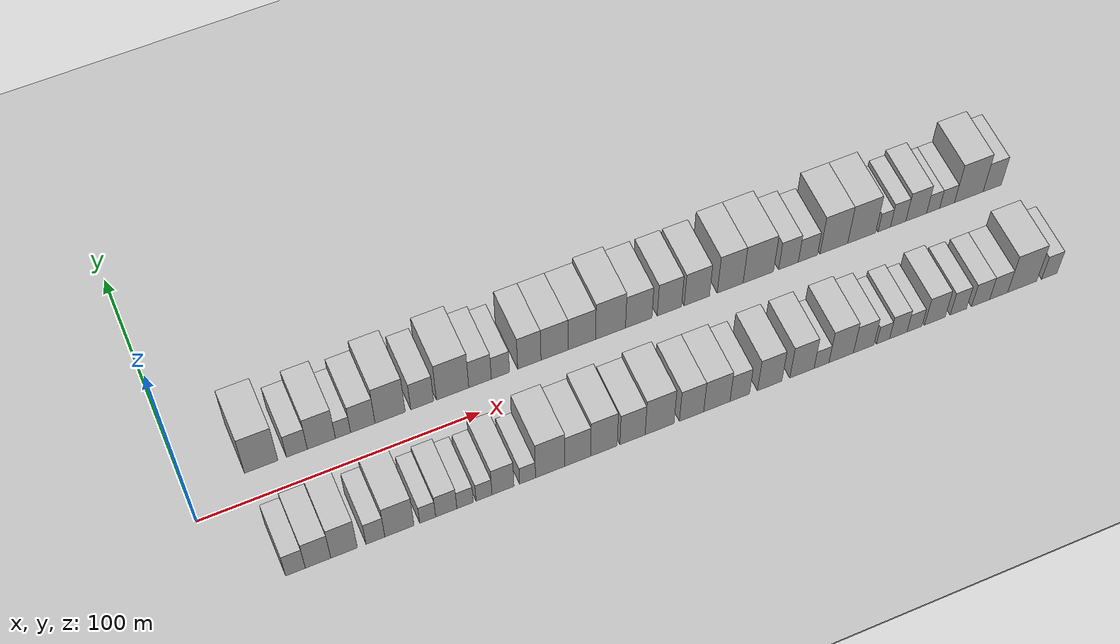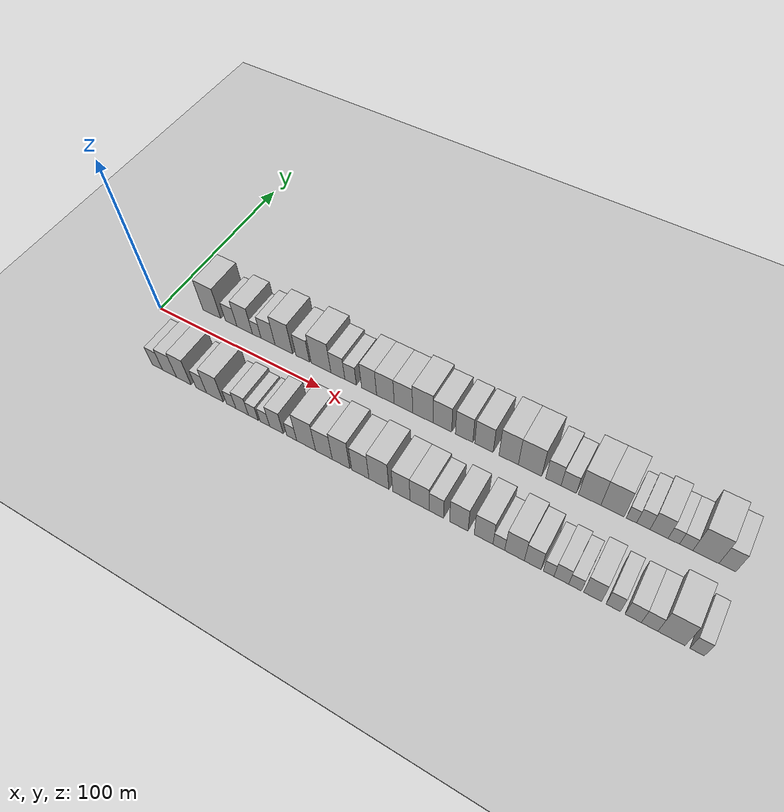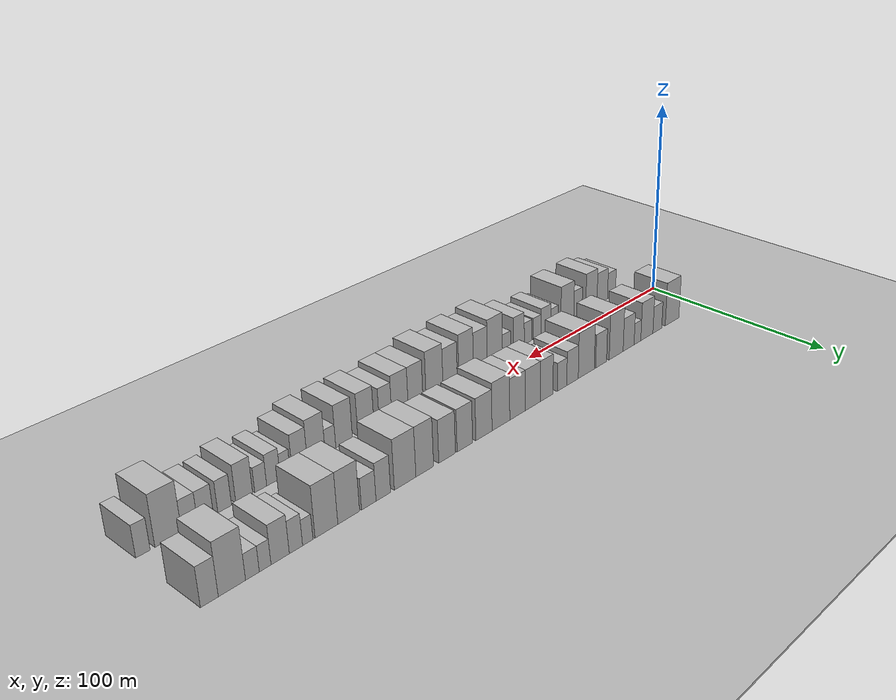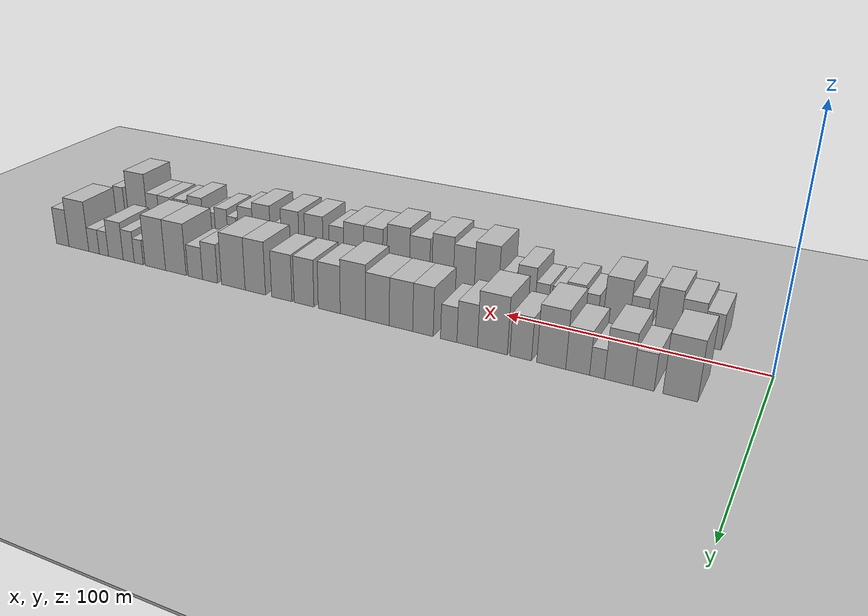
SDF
<?xml version="1.0" encoding="utf-8"?>

<sdf version="1.6">

   <world name="default">

      <gui fullscreen="0">

         <camera name="user_camera">

            <pose>-15 0 4.57585 0 0 0</pose>

            <view_controller>orbit</view_controller>

         </camera>

      </gui>

      <scene>

         <sky>

           <clouds>

             <speed>12</speed>

           </clouds>

         </sky>

         <ambient>0.4 0.4 0.4 1</ambient>

         <background>0.7 0.7 0.7 1</background>

         <shadows>1</shadows>

      </scene>

      <gravity>0 0 -9.8066</gravity>

      <magnetic_field>6e-06 2.3e-05 -4.2e-05</magnetic_field>

      <physics default="0" name="default_physics" type="ode">

         <ode>

            <solver>

               <type>quick</type>

               <iters>10</iters>

               <sor>1.0</sor>

               <use_dynamic_moi_rescaling>0</use_dynamic_moi_rescaling>

            </solver>

            <constraints>

               <cfm>0</cfm>

               <erp>0.2</erp>

               <contact_max_correcting_vel>100</contact_max_correcting_vel>

               <contact_surface_layer>0.001</contact_surface_layer>

            </constraints>

         </ode>

         <max_step_size>0.004</max_step_size>

         <real_time_factor>1</real_time_factor>

         <real_time_update_rate>250</real_time_update_rate>

      </physics>

      <light name="sun" type="directional">

         <cast_shadows>1</cast_shadows>

         <pose>0 0 10 0 0 0</pose>

         <diffuse>0.8 0.8 0.8 1</diffuse>

         <specular>0.2 0.2 0.2 1</specular>

         <attenuation>

            <range>1000</range>

            <constant>0.9</constant>

            <linear>0.01</linear>

            <quadratic>0.001</quadratic>

         </attenuation>

         <direction>-0.5 0.1 -0.9</direction>

      </light>

      <include>

         <name>ground_plane_1</name>

         <uri>model://HANNAS_ground_plane</uri>

         <pose>0 0 0  0 0 0</pose>

      </include>

      <include>

         <name>ground_plane_2</name>

         <uri>model://HANNAS_ground_plane</uri>

         <pose>100 0 0  0 0 0</pose>

      </include>

      <model name="building_1">

         <static>1</static>

         <pose frame="">25.8612 20.0000 0 0.000000 0.000000 1.570796</pose>

         <link name="link">

            <pose frame="">0 0 12.00 0 0 0</pose>

            <collision name="collision">

               <geometry>

                  <box>

                     <size>20.0000 11.7223 24.0000</size>

                  </box>

               </geometry>

               <max_contacts>10</max_contacts>

               <surface>

                  <contact>

                     <ode/>

                  </contact>

                  <bounce/>

                  <friction>

                     <torsional>

                        <ode/>

                     </torsional>

                     <ode/>

                  </friction>

               </surface>

            </collision>

            <visual name="visual">

               <cast_shadows>0</cast_shadows>

               <geometry>

                  <box>

                     <size>20.0000 11.7223 24.0000</size>

                  </box>

               </geometry>

               <material>

                  <script>

                     <uri>model://HANNAS_wall/materials/scripts</uri>

                     <uri>model://HANNAS_wall/materials/textures</uri>

                     <name>vrc/HANNAS_wall</name>

                  </script>

               </material>

            </visual>

            <self_collide>0</self_collide>

            <enable_wind>0</enable_wind>

            <kinematic>0</kinematic>

         </link>

      </model>

      <model name="building_2">

         <static>1</static>

         <pose frame="">38.4278 20.0000 0 0.000000 0.000000 1.570796</pose>

         <link name="link">

            <pose frame="">0 0 7.50 0 0 0</pose>

            <collision name="collision">

               <geometry>

                  <box>

                     <size>20.0000 7.4110 15.0000</size>

                  </box>

               </geometry>

               <max_contacts>10</max_contacts>

               <surface>

                  <contact>

                     <ode/>

                  </contact>

                  <bounce/>

                  <friction>

                     <torsional>

                        <ode/>

                     </torsional>

                     <ode/>

                  </friction>

               </surface>

            </collision>

            <visual name="visual">

               <cast_shadows>0</cast_shadows>

               <geometry>

                  <box>

                     <size>20.0000 7.4110 15.0000</size>

                  </box>

               </geometry>

               <material>

                  <script>

                     <uri>model://HANNAS_wall/materials/scripts</uri>

                     <uri>model://HANNAS_wall/materials/textures</uri>

                     <name>vrc/HANNAS_wall</name>

                  </script>

               </material>

            </visual>

            <self_collide>0</self_collide>

            <enable_wind>0</enable_wind>

            <kinematic>0</kinematic>

         </link>

      </model>

      <model name="building_3">

         <static>1</static>

         <pose frame="">47.1122 20.0000 0 0.000000 0.000000 1.570796</pose>

         <link name="link">

            <pose frame="">0 0 10.50 0 0 0</pose>

            <collision name="collision">

               <geometry>

                  <box>

                     <size>20.0000 9.9578 21.0000</size>

                  </box>

               </geometry>

               <max_contacts>10</max_contacts>

               <surface>

                  <contact>

                     <ode/>

                  </contact>

                  <bounce/>

                  <friction>

                     <torsional>

                        <ode/>

                     </torsional>

                     <ode/>

                  </friction>

               </surface>

            </collision>

            <visual name="visual">

               <cast_shadows>0</cast_shadows>

               <geometry>

                  <box>

                     <size>20.0000 9.9578 21.0000</size>

                  </box>

               </geometry>

               <material>

                  <script>

                     <uri>model://HANNAS_wall/materials/scripts</uri>

                     <uri>model://HANNAS_wall/materials/textures</uri>

                     <name>vrc/HANNAS_wall</name>

                  </script>

               </material>

            </visual>

            <self_collide>0</self_collide>

            <enable_wind>0</enable_wind>

            <kinematic>0</kinematic>

         </link>

      </model>

      <model name="building_4">

         <static>1</static>

         <pose frame="">54.7990 20.0000 0 0.000000 0.000000 1.570796</pose>

         <link name="link">

            <pose frame="">0 0 6.00 0 0 0</pose>

            <collision name="collision">

               <geometry>

                  <box>

                     <size>20.0000 5.4158 12.0000</size>

                  </box>

               </geometry>

               <max_contacts>10</max_contacts>

               <surface>

                  <contact>

                     <ode/>

                  </contact>

                  <bounce/>

                  <friction>

                     <torsional>

                        <ode/>

                     </torsional>

                     <ode/>

                  </friction>

               </surface>

            </collision>

            <visual name="visual">

               <cast_shadows>0</cast_shadows>

               <geometry>

                  <box>

                     <size>20.0000 5.4158 12.0000</size>

                  </box>

               </geometry>

               <material>

                  <script>

                     <uri>model://HANNAS_wall/materials/scripts</uri>

                     <uri>model://HANNAS_wall/materials/textures</uri>

                     <name>vrc/HANNAS_wall</name>

                  </script>

               </material>

            </visual>

            <self_collide>0</self_collide>

            <enable_wind>0</enable_wind>

            <kinematic>0</kinematic>

         </link>

      </model>

      <model name="building_5">

         <static>1</static>

         <pose frame="">61.8751 20.0000 0 0.000000 0.000000 1.570796</pose>

         <link name="link">

            <pose frame="">0 0 9.00 0 0 0</pose>

            <collision name="collision">

               <geometry>

                  <box>

                     <size>20.0000 8.7365 18.0000</size>

                  </box>

               </geometry>

               <max_contacts>10</max_contacts>

               <surface>

                  <contact>

                     <ode/>

                  </contact>

                  <bounce/>

                  <friction>

                     <torsional>

                        <ode/>

                     </torsional>

                     <ode/>

                  </friction>

               </surface>

            </collision>

            <visual name="visual">

               <cast_shadows>0</cast_shadows>

               <geometry>

                  <box>

                     <size>20.0000 8.7365 18.0000</size>

                  </box>

               </geometry>

               <material>

                  <script>

                     <uri>model://HANNAS_wall/materials/scripts</uri>

                     <uri>model://HANNAS_wall/materials/textures</uri>

                     <name>vrc/HANNAS_wall</name>

                  </script>

               </material>

            </visual>

            <self_collide>0</self_collide>

            <enable_wind>0</enable_wind>

            <kinematic>0</kinematic>

         </link>

      </model>

      <model name="building_6">

         <static>1</static>

         <pose frame="">71.6582 20.0000 0 0.000000 0.000000 1.570796</pose>

         <link name="link">

            <pose frame="">0 0 12.00 0 0 0</pose>

            <collision name="collision">

               <geometry>

                  <box>

                     <size>20.0000 10.8296 24.0000</size>

                  </box>

               </geometry>

               <max_contacts>10</max_contacts>

               <surface>

                  <contact>

                     <ode/>

                  </contact>

                  <bounce/>

                  <friction>

                     <torsional>

                        <ode/>

                     </torsional>

                     <ode/>

                  </friction>

               </surface>

            </collision>

            <visual name="visual">

               <cast_shadows>0</cast_shadows>

               <geometry>

                  <box>

                     <size>20.0000 10.8296 24.0000</size>

                  </box>

               </geometry>

               <material>

                  <script>

                     <uri>model://HANNAS_wall/materials/scripts</uri>

                     <uri>model://HANNAS_wall/materials/textures</uri>

                     <name>vrc/HANNAS_wall</name>

                  </script>

               </material>

            </visual>

            <self_collide>0</self_collide>

            <enable_wind>0</enable_wind>

            <kinematic>0</kinematic>

         </link>

      </model>

      <model name="building_7">

         <static>1</static>

         <pose frame="">83.2071 20.0000 0 0.000000 0.000000 1.570796</pose>

         <link name="link">

            <pose frame="">0 0 9.00 0 0 0</pose>

            <collision name="collision">

               <geometry>

                  <box>

                     <size>20.0000 8.2683 18.0000</size>

                  </box>

               </geometry>

               <max_contacts>10</max_contacts>

               <surface>

                  <contact>

                     <ode/>

                  </contact>

                  <bounce/>

                  <friction>

                     <torsional>

                        <ode/>

                     </torsional>

                     <ode/>

                  </friction>

               </surface>

            </collision>

            <visual name="visual">

               <cast_shadows>0</cast_shadows>

               <geometry>

                  <box>

                     <size>20.0000 8.2683 18.0000</size>

                  </box>

               </geometry>

               <material>

                  <script>

                     <uri>model://HANNAS_wall/materials/scripts</uri>

                     <uri>model://HANNAS_wall/materials/textures</uri>

                     <name>vrc/HANNAS_wall</name>

                  </script>

               </material>

            </visual>

            <self_collide>0</self_collide>

            <enable_wind>0</enable_wind>

            <kinematic>0</kinematic>

         </link>

      </model>

      <model name="building_8">

         <static>1</static>

         <pose frame="">94.2362 20.0000 0 0.000000 0.000000 1.570796</pose>

         <link name="link">

            <pose frame="">0 0 12.00 0 0 0</pose>

            <collision name="collision">

               <geometry>

                  <box>

                     <size>20.0000 11.7899 24.0000</size>

                  </box>

               </geometry>

               <max_contacts>10</max_contacts>

               <surface>

                  <contact>

                     <ode/>

                  </contact>

                  <bounce/>

                  <friction>

                     <torsional>

                        <ode/>

                     </torsional>

                     <ode/>

                  </friction>

               </surface>

            </collision>

            <visual name="visual">

               <cast_shadows>0</cast_shadows>

               <geometry>

                  <box>

                     <size>20.0000 11.7899 24.0000</size>

                  </box>

               </geometry>

               <material>

                  <script>

                     <uri>model://HANNAS_wall/materials/scripts</uri>

                     <uri>model://HANNAS_wall/materials/textures</uri>

                     <name>vrc/HANNAS_wall</name>

                  </script>

               </material>

            </visual>

            <self_collide>0</self_collide>

            <enable_wind>0</enable_wind>

            <kinematic>0</kinematic>

         </link>

      </model>

      <model name="building_9">

         <static>1</static>

         <pose frame="">104.2495 20.0000 0 0.000000 0.000000 1.570796</pose>

         <link name="link">

            <pose frame="">0 0 9.00 0 0 0</pose>

            <collision name="collision">

               <geometry>

                  <box>

                     <size>20.0000 8.2368 18.0000</size>

                  </box>

               </geometry>

               <max_contacts>10</max_contacts>

               <surface>

                  <contact>

                     <ode/>

                  </contact>

                  <bounce/>

                  <friction>

                     <torsional>

                        <ode/>

                     </torsional>

                     <ode/>

                  </friction>

               </surface>

            </collision>

            <visual name="visual">

               <cast_shadows>0</cast_shadows>

               <geometry>

                  <box>

                     <size>20.0000 8.2368 18.0000</size>

                  </box>

               </geometry>

               <material>

                  <script>

                     <uri>model://HANNAS_wall/materials/scripts</uri>

                     <uri>model://HANNAS_wall/materials/textures</uri>

                     <name>vrc/HANNAS_wall</name>

                  </script>

               </material>

            </visual>

            <self_collide>0</self_collide>

            <enable_wind>0</enable_wind>

            <kinematic>0</kinematic>

         </link>

      </model>

      <model name="building_10">

         <static>1</static>

         <pose frame="">111.7184 20.0000 0 0.000000 0.000000 1.570796</pose>

         <link name="link">

            <pose frame="">0 0 7.50 0 0 0</pose>

            <collision name="collision">

               <geometry>

                  <box>

                     <size>20.0000 6.7009 15.0000</size>

                  </box>

               </geometry>

               <max_contacts>10</max_contacts>

               <surface>

                  <contact>

                     <ode/>

                  </contact>

                  <bounce/>

                  <friction>

                     <torsional>

                        <ode/>

                     </torsional>

                     <ode/>

                  </friction>

               </surface>

            </collision>

            <visual name="visual">

               <cast_shadows>0</cast_shadows>

               <geometry>

                  <box>

                     <size>20.0000 6.7009 15.0000</size>

                  </box>

               </geometry>

               <material>

                  <script>

                     <uri>model://HANNAS_wall/materials/scripts</uri>

                     <uri>model://HANNAS_wall/materials/textures</uri>

                     <name>vrc/HANNAS_wall</name>

                  </script>

               </material>

            </visual>

            <self_collide>0</self_collide>

            <enable_wind>0</enable_wind>

            <kinematic>0</kinematic>

         </link>

      </model>

      <model name="building_11">

         <static>1</static>

         <pose frame="">122.3707 20.0000 0 0.000000 0.000000 1.570796</pose>

         <link name="link">

            <pose frame="">0 0 10.50 0 0 0</pose>

            <collision name="collision">

               <geometry>

                  <box>

                     <size>20.0000 8.6038 21.0000</size>

                  </box>

               </geometry>

               <max_contacts>10</max_contacts>

               <surface>

                  <contact>

                     <ode/>

                  </contact>

                  <bounce/>

                  <friction>

                     <torsional>

                        <ode/>

                     </torsional>

                     <ode/>

                  </friction>

               </surface>

            </collision>

            <visual name="visual">

               <cast_shadows>0</cast_shadows>

               <geometry>

                  <box>

                     <size>20.0000 8.6038 21.0000</size>

                  </box>

               </geometry>

               <material>

                  <script>

                     <uri>model://HANNAS_wall/materials/scripts</uri>

                     <uri>model://HANNAS_wall/materials/textures</uri>

                     <name>vrc/HANNAS_wall</name>

                  </script>

               </material>

            </visual>

            <self_collide>0</self_collide>

            <enable_wind>0</enable_wind>

            <kinematic>0</kinematic>

         </link>

      </model>

      <model name="building_12">

         <static>1</static>

         <pose frame="">131.6753 20.0000 0 0.000000 0.000000 1.570796</pose>

         <link name="link">

            <pose frame="">0 0 10.50 0 0 0</pose>

            <collision name="collision">

               <geometry>

                  <box>

                     <size>20.0000 10.0054 21.0000</size>

                  </box>

               </geometry>

               <max_contacts>10</max_contacts>

               <surface>

                  <contact>

                     <ode/>

                  </contact>

                  <bounce/>

                  <friction>

                     <torsional>

                        <ode/>

                     </torsional>

                     <ode/>

                  </friction>

               </surface>

            </collision>

            <visual name="visual">

               <cast_shadows>0</cast_shadows>

               <geometry>

                  <box>

                     <size>20.0000 10.0054 21.0000</size>

                  </box>

               </geometry>

               <material>

                  <script>

                     <uri>model://HANNAS_wall/materials/scripts</uri>

                     <uri>model://HANNAS_wall/materials/textures</uri>

                     <name>vrc/HANNAS_wall</name>

                  </script>

               </material>

            </visual>

            <self_collide>0</self_collide>

            <enable_wind>0</enable_wind>

            <kinematic>0</kinematic>

         </link>

      </model>

      <model name="building_13">

         <static>1</static>

         <pose frame="">141.8260 20.0000 0 0.000000 0.000000 1.570796</pose>

         <link name="link">

            <pose frame="">0 0 10.50 0 0 0</pose>

            <collision name="collision">

               <geometry>

                  <box>

                     <size>20.0000 10.2962 21.0000</size>

                  </box>

               </geometry>

               <max_contacts>10</max_contacts>

               <surface>

                  <contact>

                     <ode/>

                  </contact>

                  <bounce/>

                  <friction>

                     <torsional>

                        <ode/>

                     </torsional>

                     <ode/>

                  </friction>

               </surface>

            </collision>

            <visual name="visual">

               <cast_shadows>0</cast_shadows>

               <geometry>

                  <box>

                     <size>20.0000 10.2962 21.0000</size>

                  </box>

               </geometry>

               <material>

                  <script>

                     <uri>model://HANNAS_wall/materials/scripts</uri>

                     <uri>model://HANNAS_wall/materials/textures</uri>

                     <name>vrc/HANNAS_wall</name>

                  </script>

               </material>

            </visual>

            <self_collide>0</self_collide>

            <enable_wind>0</enable_wind>

            <kinematic>0</kinematic>

         </link>

      </model>

      <model name="building_14">

         <static>1</static>

         <pose frame="">152.6036 20.0000 0 0.000000 0.000000 1.570796</pose>

         <link name="link">

            <pose frame="">0 0 12.00 0 0 0</pose>

            <collision name="collision">

               <geometry>

                  <box>

                     <size>20.0000 11.2589 24.0000</size>

                  </box>

               </geometry>

               <max_contacts>10</max_contacts>

               <surface>

                  <contact>

                     <ode/>

                  </contact>

                  <bounce/>

                  <friction>

                     <torsional>

                        <ode/>

                     </torsional>

                     <ode/>

                  </friction>

               </surface>

            </collision>

            <visual name="visual">

               <cast_shadows>0</cast_shadows>

               <geometry>

                  <box>

                     <size>20.0000 11.2589 24.0000</size>

                  </box>

               </geometry>

               <material>

                  <script>

                     <uri>model://HANNAS_wall/materials/scripts</uri>

                     <uri>model://HANNAS_wall/materials/textures</uri>

                     <name>vrc/HANNAS_wall</name>

                  </script>

               </material>

            </visual>

            <self_collide>0</self_collide>

            <enable_wind>0</enable_wind>

            <kinematic>0</kinematic>

         </link>

      </model>

      <model name="building_15">

         <static>1</static>

         <pose frame="">163.2316 20.0000 0 0.000000 0.000000 1.570796</pose>

         <link name="link">

            <pose frame="">0 0 10.50 0 0 0</pose>

            <collision name="collision">

               <geometry>

                  <box>

                     <size>20.0000 9.9971 21.0000</size>

                  </box>

               </geometry>

               <max_contacts>10</max_contacts>

               <surface>

                  <contact>

                     <ode/>

                  </contact>

                  <bounce/>

                  <friction>

                     <torsional>

                        <ode/>

                     </torsional>

                     <ode/>

                  </friction>

               </surface>

            </collision>

            <visual name="visual">

               <cast_shadows>0</cast_shadows>

               <geometry>

                  <box>

                     <size>20.0000 9.9971 21.0000</size>

                  </box>

               </geometry>

               <material>

                  <script>

                     <uri>model://HANNAS_wall/materials/scripts</uri>

                     <uri>model://HANNAS_wall/materials/textures</uri>

                     <name>vrc/HANNAS_wall</name>

                  </script>

               </material>

            </visual>

            <self_collide>0</self_collide>

            <enable_wind>0</enable_wind>

            <kinematic>0</kinematic>

         </link>

      </model>

      <model name="building_16">

         <static>1</static>

         <pose frame="">174.8527 20.0000 0 0.000000 0.000000 1.570796</pose>

         <link name="link">

            <pose frame="">0 0 10.50 0 0 0</pose>

            <collision name="collision">

               <geometry>

                  <box>

                     <size>20.0000 9.2451 21.0000</size>

                  </box>

               </geometry>

               <max_contacts>10</max_contacts>

               <surface>

                  <contact>

                     <ode/>

                  </contact>

                  <bounce/>

                  <friction>

                     <torsional>

                        <ode/>

                     </torsional>

                     <ode/>

                  </friction>

               </surface>

            </collision>

            <visual name="visual">

               <cast_shadows>0</cast_shadows>

               <geometry>

                  <box>

                     <size>20.0000 9.2451 21.0000</size>

                  </box>

               </geometry>

               <material>

                  <script>

                     <uri>model://HANNAS_wall/materials/scripts</uri>

                     <uri>model://HANNAS_wall/materials/textures</uri>

                     <name>vrc/HANNAS_wall</name>

                  </script>

               </material>

            </visual>

            <self_collide>0</self_collide>

            <enable_wind>0</enable_wind>

            <kinematic>0</kinematic>

         </link>

      </model>

      <model name="building_17">

         <static>1</static>

         <pose frame="">185.3069 20.0000 0 0.000000 0.000000 1.570796</pose>

         <link name="link">

            <pose frame="">0 0 10.50 0 0 0</pose>

            <collision name="collision">

               <geometry>

                  <box>

                     <size>20.0000 9.6634 21.0000</size>

                  </box>

               </geometry>

               <max_contacts>10</max_contacts>

               <surface>

                  <contact>

                     <ode/>

                  </contact>

                  <bounce/>

                  <friction>

                     <torsional>

                        <ode/>

                     </torsional>

                     <ode/>

                  </friction>

               </surface>

            </collision>

            <visual name="visual">

               <cast_shadows>0</cast_shadows>

               <geometry>

                  <box>

                     <size>20.0000 9.6634 21.0000</size>

                  </box>

               </geometry>

               <material>

                  <script>

                     <uri>model://HANNAS_wall/materials/scripts</uri>

                     <uri>model://HANNAS_wall/materials/textures</uri>

                     <name>vrc/HANNAS_wall</name>

                  </script>

               </material>

            </visual>

            <self_collide>0</self_collide>

            <enable_wind>0</enable_wind>

            <kinematic>0</kinematic>

         </link>

      </model>

      <model name="building_18">

         <static>1</static>

         <pose frame="">198.1085 20.0000 0 0.000000 0.000000 1.570796</pose>

         <link name="link">

            <pose frame="">0 0 12.00 0 0 0</pose>

            <collision name="collision">

               <geometry>

                  <box>

                     <size>20.0000 9.9397 24.0000</size>

                  </box>

               </geometry>

               <max_contacts>10</max_contacts>

               <surface>

                  <contact>

                     <ode/>

                  </contact>

                  <bounce/>

                  <friction>

                     <torsional>

                        <ode/>

                     </torsional>

                     <ode/>

                  </friction>

               </surface>

            </collision>

            <visual name="visual">

               <cast_shadows>0</cast_shadows>

               <geometry>

                  <box>

                     <size>20.0000 9.9397 24.0000</size>

                  </box>

               </geometry>

               <material>

                  <script>

                     <uri>model://HANNAS_wall/materials/scripts</uri>

                     <uri>model://HANNAS_wall/materials/textures</uri>

                     <name>vrc/HANNAS_wall</name>

                  </script>

               </material>

            </visual>

            <self_collide>0</self_collide>

            <enable_wind>0</enable_wind>

            <kinematic>0</kinematic>

         </link>

      </model>

      <model name="building_19">

         <static>1</static>

         <pose frame="">208.9604 20.0000 0 0.000000 0.000000 1.570796</pose>

         <link name="link">

            <pose frame="">0 0 12.00 0 0 0</pose>

            <collision name="collision">

               <geometry>

                  <box>

                     <size>20.0000 11.7642 24.0000</size>

                  </box>

               </geometry>

               <max_contacts>10</max_contacts>

               <surface>

                  <contact>

                     <ode/>

                  </contact>

                  <bounce/>

                  <friction>

                     <torsional>

                        <ode/>

                     </torsional>

                     <ode/>

                  </friction>

               </surface>

            </collision>

            <visual name="visual">

               <cast_shadows>0</cast_shadows>

               <geometry>

                  <box>

                     <size>20.0000 11.7642 24.0000</size>

                  </box>

               </geometry>

               <material>

                  <script>

                     <uri>model://HANNAS_wall/materials/scripts</uri>

                     <uri>model://HANNAS_wall/materials/textures</uri>

                     <name>vrc/HANNAS_wall</name>

                  </script>

               </material>

            </visual>

            <self_collide>0</self_collide>

            <enable_wind>0</enable_wind>

            <kinematic>0</kinematic>

         </link>

      </model>

      <model name="building_20">

         <static>1</static>

         <pose frame="">220.6789 20.0000 0 0.000000 0.000000 1.570796</pose>

         <link name="link">

            <pose frame="">0 0 9.00 0 0 0</pose>

            <collision name="collision">

               <geometry>

                  <box>

                     <size>20.0000 7.6727 18.0000</size>

                  </box>

               </geometry>

               <max_contacts>10</max_contacts>

               <surface>

                  <contact>

                     <ode/>

                  </contact>

                  <bounce/>

                  <friction>

                     <torsional>

                        <ode/>

                     </torsional>

                     <ode/>

                  </friction>

               </surface>

            </collision>

            <visual name="visual">

               <cast_shadows>0</cast_shadows>

               <geometry>

                  <box>

                     <size>20.0000 7.6727 18.0000</size>

                  </box>

               </geometry>

               <material>

                  <script>

                     <uri>model://HANNAS_wall/materials/scripts</uri>

                     <uri>model://HANNAS_wall/materials/textures</uri>

                     <name>vrc/HANNAS_wall</name>

                  </script>

               </material>

            </visual>

            <self_collide>0</self_collide>

            <enable_wind>0</enable_wind>

            <kinematic>0</kinematic>

         </link>

      </model>

      <model name="building_21">

         <static>1</static>

         <pose frame="">228.2584 20.0000 0 0.000000 0.000000 1.570796</pose>

         <link name="link">

            <pose frame="">0 0 7.50 0 0 0</pose>

            <collision name="collision">

               <geometry>

                  <box>

                     <size>20.0000 7.4864 15.0000</size>

                  </box>

               </geometry>

               <max_contacts>10</max_contacts>

               <surface>

                  <contact>

                     <ode/>

                  </contact>

                  <bounce/>

                  <friction>

                     <torsional>

                        <ode/>

                     </torsional>

                     <ode/>

                  </friction>

               </surface>

            </collision>

            <visual name="visual">

               <cast_shadows>0</cast_shadows>

               <geometry>

                  <box>

                     <size>20.0000 7.4864 15.0000</size>

                  </box>

               </geometry>

               <material>

                  <script>

                     <uri>model://HANNAS_wall/materials/scripts</uri>

                     <uri>model://HANNAS_wall/materials/textures</uri>

                     <name>vrc/HANNAS_wall</name>

                  </script>

               </material>

            </visual>

            <self_collide>0</self_collide>

            <enable_wind>0</enable_wind>

            <kinematic>0</kinematic>

         </link>

      </model>

      <model name="building_22">

         <static>1</static>

         <pose frame="">238.4389 20.0000 0 0.000000 0.000000 1.570796</pose>

         <link name="link">

            <pose frame="">0 0 12.00 0 0 0</pose>

            <collision name="collision">

               <geometry>

                  <box>

                     <size>20.0000 10.8745 24.0000</size>

                  </box>

               </geometry>

               <max_contacts>10</max_contacts>

               <surface>

                  <contact>

                     <ode/>

                  </contact>

                  <bounce/>

                  <friction>

                     <torsional>

                        <ode/>

                     </torsional>

                     <ode/>

                  </friction>

               </surface>

            </collision>

            <visual name="visual">

               <cast_shadows>0</cast_shadows>

               <geometry>

                  <box>

                     <size>20.0000 10.8745 24.0000</size>

                  </box>

               </geometry>

               <material>

                  <script>

                     <uri>model://HANNAS_wall/materials/scripts</uri>

                     <uri>model://HANNAS_wall/materials/textures</uri>

                     <name>vrc/HANNAS_wall</name>

                  </script>

               </material>

            </visual>

            <self_collide>0</self_collide>

            <enable_wind>0</enable_wind>

            <kinematic>0</kinematic>

         </link>

      </model>

      <model name="building_23">

         <static>1</static>

         <pose frame="">249.3946 20.0000 0 0.000000 0.000000 1.570796</pose>

         <link name="link">

            <pose frame="">0 0 12.00 0 0 0</pose>

            <collision name="collision">

               <geometry>

                  <box>

                     <size>20.0000 11.0370 24.0000</size>

                  </box>

               </geometry>

               <max_contacts>10</max_contacts>

               <surface>

                  <contact>

                     <ode/>

                  </contact>

                  <bounce/>

                  <friction>

                     <torsional>

                        <ode/>

                     </torsional>

                     <ode/>

                  </friction>

               </surface>

            </collision>

            <visual name="visual">

               <cast_shadows>0</cast_shadows>

               <geometry>

                  <box>

                     <size>20.0000 11.0370 24.0000</size>

                  </box>

               </geometry>

               <material>

                  <script>

                     <uri>model://HANNAS_wall/materials/scripts</uri>

                     <uri>model://HANNAS_wall/materials/textures</uri>

                     <name>vrc/HANNAS_wall</name>

                  </script>

               </material>

            </visual>

            <self_collide>0</self_collide>

            <enable_wind>0</enable_wind>

            <kinematic>0</kinematic>

         </link>

      </model>

      <model name="building_24">

         <static>1</static>

         <pose frame="">258.3579 20.0000 0 0.000000 0.000000 1.570796</pose>

         <link name="link">

            <pose frame="">0 0 6.00 0 0 0</pose>

            <collision name="collision">

               <geometry>

                  <box>

                     <size>20.0000 4.8894 12.0000</size>

                  </box>

               </geometry>

               <max_contacts>10</max_contacts>

               <surface>

                  <contact>

                     <ode/>

                  </contact>

                  <bounce/>

                  <friction>

                     <torsional>

                        <ode/>

                     </torsional>

                     <ode/>

                  </friction>

               </surface>

            </collision>

            <visual name="visual">

               <cast_shadows>0</cast_shadows>

               <geometry>

                  <box>

                     <size>20.0000 4.8894 12.0000</size>

                  </box>

               </geometry>

               <material>

                  <script>

                     <uri>model://HANNAS_wall/materials/scripts</uri>

                     <uri>model://HANNAS_wall/materials/textures</uri>

                     <name>vrc/HANNAS_wall</name>

                  </script>

               </material>

            </visual>

            <self_collide>0</self_collide>

            <enable_wind>0</enable_wind>

            <kinematic>0</kinematic>

         </link>

      </model>

      <model name="building_25">

         <static>1</static>

         <pose frame="">263.8838 20.0000 0 0.000000 0.000000 1.570796</pose>

         <link name="link">

            <pose frame="">0 0 7.50 0 0 0</pose>

            <collision name="collision">

               <geometry>

                  <box>

                     <size>20.0000 6.1624 15.0000</size>

                  </box>

               </geometry>

               <max_contacts>10</max_contacts>

               <surface>

                  <contact>

                     <ode/>

                  </contact>

                  <bounce/>

                  <friction>

                     <torsional>

                        <ode/>

                     </torsional>

                     <ode/>

                  </friction>

               </surface>

            </collision>

            <visual name="visual">

               <cast_shadows>0</cast_shadows>

               <geometry>

                  <box>

                     <size>20.0000 6.1624 15.0000</size>

                  </box>

               </geometry>

               <material>

                  <script>

                     <uri>model://HANNAS_wall/materials/scripts</uri>

                     <uri>model://HANNAS_wall/materials/textures</uri>

                     <name>vrc/HANNAS_wall</name>

                  </script>

               </material>

            </visual>

            <self_collide>0</self_collide>

            <enable_wind>0</enable_wind>

            <kinematic>0</kinematic>

         </link>

      </model>

      <model name="building_26">

         <static>1</static>

         <pose frame="">271.0997 20.0000 0 0.000000 0.000000 1.570796</pose>

         <link name="link">

            <pose frame="">0 0 9.00 0 0 0</pose>

            <collision name="collision">

               <geometry>

                  <box>

                     <size>20.0000 8.2695 18.0000</size>

                  </box>

               </geometry>

               <max_contacts>10</max_contacts>

               <surface>

                  <contact>

                     <ode/>

                  </contact>

                  <bounce/>

                  <friction>

                     <torsional>

                        <ode/>

                     </torsional>

                     <ode/>

                  </friction>

               </surface>

            </collision>

            <visual name="visual">

               <cast_shadows>0</cast_shadows>

               <geometry>

                  <box>

                     <size>20.0000 8.2695 18.0000</size>

                  </box>

               </geometry>

               <material>

                  <script>

                     <uri>model://HANNAS_wall/materials/scripts</uri>

                     <uri>model://HANNAS_wall/materials/textures</uri>

                     <name>vrc/HANNAS_wall</name>

                  </script>

               </material>

            </visual>

            <self_collide>0</self_collide>

            <enable_wind>0</enable_wind>

            <kinematic>0</kinematic>

         </link>

      </model>

      <model name="building_27">

         <static>1</static>

         <pose frame="">277.8459 20.0000 0 0.000000 0.000000 1.570796</pose>

         <link name="link">

            <pose frame="">0 0 6.00 0 0 0</pose>

            <collision name="collision">

               <geometry>

                  <box>

                     <size>20.0000 5.2229 12.0000</size>

                  </box>

               </geometry>

               <max_contacts>10</max_contacts>

               <surface>

                  <contact>

                     <ode/>

                  </contact>

                  <bounce/>

                  <friction>

                     <torsional>

                        <ode/>

                     </torsional>

                     <ode/>

                  </friction>

               </surface>

            </collision>

            <visual name="visual">

               <cast_shadows>0</cast_shadows>

               <geometry>

                  <box>

                     <size>20.0000 5.2229 12.0000</size>

                  </box>

               </geometry>

               <material>

                  <script>

                     <uri>model://HANNAS_wall/materials/scripts</uri>

                     <uri>model://HANNAS_wall/materials/textures</uri>

                     <name>vrc/HANNAS_wall</name>

                  </script>

               </material>

            </visual>

            <self_collide>0</self_collide>

            <enable_wind>0</enable_wind>

            <kinematic>0</kinematic>

         </link>

      </model>

      <model name="building_28">

         <static>1</static>

         <pose frame="">283.4523 20.0000 0 0.000000 0.000000 1.570796</pose>

         <link name="link">

            <pose frame="">0 0 6.00 0 0 0</pose>

            <collision name="collision">

               <geometry>

                  <box>

                     <size>20.0000 5.9900 12.0000</size>

                  </box>

               </geometry>

               <max_contacts>10</max_contacts>

               <surface>

                  <contact>

                     <ode/>

                  </contact>

                  <bounce/>

                  <friction>

                     <torsional>

                        <ode/>

                     </torsional>

                     <ode/>

                  </friction>

               </surface>

            </collision>

            <visual name="visual">

               <cast_shadows>0</cast_shadows>

               <geometry>

                  <box>

                     <size>20.0000 5.9900 12.0000</size>

                  </box>

               </geometry>

               <material>

                  <script>

                     <uri>model://HANNAS_wall/materials/scripts</uri>

                     <uri>model://HANNAS_wall/materials/textures</uri>

                     <name>vrc/HANNAS_wall</name>

                  </script>

               </material>

            </visual>

            <self_collide>0</self_collide>

            <enable_wind>0</enable_wind>

            <kinematic>0</kinematic>

         </link>

      </model>

      <model name="building_29">

         <static>1</static>

         <pose frame="">292.2314 20.0000 0 0.000000 0.000000 1.570796</pose>

         <link name="link">

            <pose frame="">0 0 12.00 0 0 0</pose>

            <collision name="collision">

               <geometry>

                  <box>

                     <size>20.0000 11.5681 24.0000</size>

                  </box>

               </geometry>

               <max_contacts>10</max_contacts>

               <surface>

                  <contact>

                     <ode/>

                  </contact>

                  <bounce/>

                  <friction>

                     <torsional>

                        <ode/>

                     </torsional>

                     <ode/>

                  </friction>

               </surface>

            </collision>

            <visual name="visual">

               <cast_shadows>0</cast_shadows>

               <geometry>

                  <box>

                     <size>20.0000 11.5681 24.0000</size>

                  </box>

               </geometry>

               <material>

                  <script>

                     <uri>model://HANNAS_wall/materials/scripts</uri>

                     <uri>model://HANNAS_wall/materials/textures</uri>

                     <name>vrc/HANNAS_wall</name>

                  </script>

               </material>

            </visual>

            <self_collide>0</self_collide>

            <enable_wind>0</enable_wind>

            <kinematic>0</kinematic>

         </link>

      </model>

      <model name="building_30">

         <static>1</static>

         <pose frame="">301.7068 20.0000 0 0.000000 0.000000 1.570796</pose>

         <link name="link">

            <pose frame="">0 0 9.00 0 0 0</pose>

            <collision name="collision">

               <geometry>

                  <box>

                     <size>20.0000 7.3826 18.0000</size>

                  </box>

               </geometry>

               <max_contacts>10</max_contacts>

               <surface>

                  <contact>

                     <ode/>

                  </contact>

                  <bounce/>

                  <friction>

                     <torsional>

                        <ode/>

                     </torsional>

                     <ode/>

                  </friction>

               </surface>

            </collision>

            <visual name="visual">

               <cast_shadows>0</cast_shadows>

               <geometry>

                  <box>

                     <size>20.0000 7.3826 18.0000</size>

                  </box>

               </geometry>

               <material>

                  <script>

                     <uri>model://HANNAS_wall/materials/scripts</uri>

                     <uri>model://HANNAS_wall/materials/textures</uri>

                     <name>vrc/HANNAS_wall</name>

                  </script>

               </material>

            </visual>

            <self_collide>0</self_collide>

            <enable_wind>0</enable_wind>

            <kinematic>0</kinematic>

         </link>

      </model>

      <model name="building_31">

         <static>1</static>

         <pose frame="">23.3865 -20.0000 0 0.000000 0.000000 1.570796</pose>

         <link name="link">

            <pose frame="">0 0 7.50 0 0 0</pose>

            <collision name="collision">

               <geometry>

                  <box>

                     <size>20.0000 6.7730 15.0000</size>

                  </box>

               </geometry>

               <max_contacts>10</max_contacts>

               <surface>

                  <contact>

                     <ode/>

                  </contact>

                  <bounce/>

                  <friction>

                     <torsional>

                        <ode/>

                     </torsional>

                     <ode/>

                  </friction>

               </surface>

            </collision>

            <visual name="visual">

               <cast_shadows>0</cast_shadows>

               <geometry>

                  <box>

                     <size>20.0000 6.7730 15.0000</size>

                  </box>

               </geometry>

               <material>

                  <script>

                     <uri>model://HANNAS_wall/materials/scripts</uri>

                     <uri>model://HANNAS_wall/materials/textures</uri>

                     <name>vrc/HANNAS_wall</name>

                  </script>

               </material>

            </visual>

            <self_collide>0</self_collide>

            <enable_wind>0</enable_wind>

            <kinematic>0</kinematic>

         </link>

      </model>

      <model name="building_32">

         <static>1</static>

         <pose frame="">31.1684 -20.0000 0 0.000000 0.000000 1.570796</pose>

         <link name="link">

            <pose frame="">0 0 9.00 0 0 0</pose>

            <collision name="collision">

               <geometry>

                  <box>

                     <size>20.0000 8.7908 18.0000</size>

                  </box>

               </geometry>

               <max_contacts>10</max_contacts>

               <surface>

                  <contact>

                     <ode/>

                  </contact>

                  <bounce/>

                  <friction>

                     <torsional>

                        <ode/>

                     </torsional>

                     <ode/>

                  </friction>

               </surface>

            </collision>

            <visual name="visual">

               <cast_shadows>0</cast_shadows>

               <geometry>

                  <box>

                     <size>20.0000 8.7908 18.0000</size>

                  </box>

               </geometry>

               <material>

                  <script>

                     <uri>model://HANNAS_wall/materials/scripts</uri>

                     <uri>model://HANNAS_wall/materials/textures</uri>

                     <name>vrc/HANNAS_wall</name>

                  </script>

               </material>

            </visual>

            <self_collide>0</self_collide>

            <enable_wind>0</enable_wind>

            <kinematic>0</kinematic>

         </link>

      </model>

      <model name="building_33">

         <static>1</static>

         <pose frame="">40.1596 -20.0000 0 0.000000 0.000000 1.570796</pose>

         <link name="link">

            <pose frame="">0 0 10.50 0 0 0</pose>

            <collision name="collision">

               <geometry>

                  <box>

                     <size>20.0000 9.1915 21.0000</size>

                  </box>

               </geometry>

               <max_contacts>10</max_contacts>

               <surface>

                  <contact>

                     <ode/>

                  </contact>

                  <bounce/>

                  <friction>

                     <torsional>

                        <ode/>

                     </torsional>

                     <ode/>

                  </friction>

               </surface>

            </collision>

            <visual name="visual">

               <cast_shadows>0</cast_shadows>

               <geometry>

                  <box>

                     <size>20.0000 9.1915 21.0000</size>

                  </box>

               </geometry>

               <material>

                  <script>

                     <uri>model://HANNAS_wall/materials/scripts</uri>

                     <uri>model://HANNAS_wall/materials/textures</uri>

                     <name>vrc/HANNAS_wall</name>

                  </script>

               </material>

            </visual>

            <self_collide>0</self_collide>

            <enable_wind>0</enable_wind>

            <kinematic>0</kinematic>

         </link>

      </model>

      <model name="building_34">

         <static>1</static>

         <pose frame="">51.0352 -20.0000 0 0.000000 0.000000 1.570796</pose>

         <link name="link">

            <pose frame="">0 0 7.50 0 0 0</pose>

            <collision name="collision">

               <geometry>

                  <box>

                     <size>20.0000 6.5596 15.0000</size>

                  </box>

               </geometry>

               <max_contacts>10</max_contacts>

               <surface>

                  <contact>

                     <ode/>

                  </contact>

                  <bounce/>

                  <friction>

                     <torsional>

                        <ode/>

                     </torsional>

                     <ode/>

                  </friction>

               </surface>

            </collision>

            <visual name="visual">

               <cast_shadows>0</cast_shadows>

               <geometry>

                  <box>

                     <size>20.0000 6.5596 15.0000</size>

                  </box>

               </geometry>

               <material>

                  <script>

                     <uri>model://HANNAS_wall/materials/scripts</uri>

                     <uri>model://HANNAS_wall/materials/textures</uri>

                     <name>vrc/HANNAS_wall</name>

                  </script>

               </material>

            </visual>

            <self_collide>0</self_collide>

            <enable_wind>0</enable_wind>

            <kinematic>0</kinematic>

         </link>

      </model>

      <model name="building_35">

         <static>1</static>

         <pose frame="">59.4114 -20.0000 0 0.000000 0.000000 1.570796</pose>

         <link name="link">

            <pose frame="">0 0 10.50 0 0 0</pose>

            <collision name="collision">

               <geometry>

                  <box>

                     <size>20.0000 10.1926 21.0000</size>

                  </box>

               </geometry>

               <max_contacts>10</max_contacts>

               <surface>

                  <contact>

                     <ode/>

                  </contact>

                  <bounce/>

                  <friction>

                     <torsional>

                        <ode/>

                     </torsional>

                     <ode/>

                  </friction>

               </surface>

            </collision>

            <visual name="visual">

               <cast_shadows>0</cast_shadows>

               <geometry>

                  <box>

                     <size>20.0000 10.1926 21.0000</size>

                  </box>

               </geometry>

               <material>

                  <script>

                     <uri>model://HANNAS_wall/materials/scripts</uri>

                     <uri>model://HANNAS_wall/materials/textures</uri>

                     <name>vrc/HANNAS_wall</name>

                  </script>

               </material>

            </visual>

            <self_collide>0</self_collide>

            <enable_wind>0</enable_wind>

            <kinematic>0</kinematic>

         </link>

      </model>

      <model name="building_36">

         <static>1</static>

         <pose frame="">69.3150 -20.0000 0 0.000000 0.000000 1.570796</pose>

         <link name="link">

            <pose frame="">0 0 6.00 0 0 0</pose>

            <collision name="collision">

               <geometry>

                  <box>

                     <size>20.0000 5.6146 12.0000</size>

                  </box>

               </geometry>

               <max_contacts>10</max_contacts>

               <surface>

                  <contact>

                     <ode/>

                  </contact>

                  <bounce/>

                  <friction>

                     <torsional>

                        <ode/>

                     </torsional>

                     <ode/>

                  </friction>

               </surface>

            </collision>

            <visual name="visual">

               <cast_shadows>0</cast_shadows>

               <geometry>

                  <box>

                     <size>20.0000 5.6146 12.0000</size>

                  </box>

               </geometry>

               <material>

                  <script>

                     <uri>model://HANNAS_wall/materials/scripts</uri>

                     <uri>model://HANNAS_wall/materials/textures</uri>

                     <name>vrc/HANNAS_wall</name>

                  </script>

               </material>

            </visual>

            <self_collide>0</self_collide>

            <enable_wind>0</enable_wind>

            <kinematic>0</kinematic>

         </link>

      </model>

      <model name="building_37">

         <static>1</static>

         <pose frame="">75.8591 -20.0000 0 0.000000 0.000000 1.570796</pose>

         <link name="link">

            <pose frame="">0 0 7.50 0 0 0</pose>

            <collision name="collision">

               <geometry>

                  <box>

                     <size>20.0000 7.4736 15.0000</size>

                  </box>

               </geometry>

               <max_contacts>10</max_contacts>

               <surface>

                  <contact>

                     <ode/>

                  </contact>

                  <bounce/>

                  <friction>

                     <torsional>

                        <ode/>

                     </torsional>

                     <ode/>

                  </friction>

               </surface>

            </collision>

            <visual name="visual">

               <cast_shadows>0</cast_shadows>

               <geometry>

                  <box>

                     <size>20.0000 7.4736 15.0000</size>

                  </box>

               </geometry>

               <material>

                  <script>

                     <uri>model://HANNAS_wall/materials/scripts</uri>

                     <uri>model://HANNAS_wall/materials/textures</uri>

                     <name>vrc/HANNAS_wall</name>

                  </script>

               </material>

            </visual>

            <self_collide>0</self_collide>

            <enable_wind>0</enable_wind>

            <kinematic>0</kinematic>

         </link>

      </model>

      <model name="building_38">

         <static>1</static>

         <pose frame="">82.4997 -20.0000 0 0.000000 0.000000 1.570796</pose>

         <link name="link">

            <pose frame="">0 0 6.00 0 0 0</pose>

            <collision name="collision">

               <geometry>

                  <box>

                     <size>20.0000 5.8074 12.0000</size>

                  </box>

               </geometry>

               <max_contacts>10</max_contacts>

               <surface>

                  <contact>

                     <ode/>

                  </contact>

                  <bounce/>

                  <friction>

                     <torsional>

                        <ode/>

                     </torsional>

                     <ode/>

                  </friction>

               </surface>

            </collision>

            <visual name="visual">

               <cast_shadows>0</cast_shadows>

               <geometry>

                  <box>

                     <size>20.0000 5.8074 12.0000</size>

                  </box>

               </geometry>

               <material>

                  <script>

                     <uri>model://HANNAS_wall/materials/scripts</uri>

                     <uri>model://HANNAS_wall/materials/textures</uri>

                     <name>vrc/HANNAS_wall</name>

                  </script>

               </material>

            </visual>

            <self_collide>0</self_collide>

            <enable_wind>0</enable_wind>

            <kinematic>0</kinematic>

         </link>

      </model>

      <model name="building_39">

         <static>1</static>

         <pose frame="">89.2289 -20.0000 0 0.000000 0.000000 1.570796</pose>

         <link name="link">

            <pose frame="">0 0 6.00 0 0 0</pose>

            <collision name="collision">

               <geometry>

                  <box>

                     <size>20.0000 5.6512 12.0000</size>

                  </box>

               </geometry>

               <max_contacts>10</max_contacts>

               <surface>

                  <contact>

                     <ode/>

                  </contact>

                  <bounce/>

                  <friction>

                     <torsional>

                        <ode/>

                     </torsional>

                     <ode/>

                  </friction>

               </surface>

            </collision>

            <visual name="visual">

               <cast_shadows>0</cast_shadows>

               <geometry>

                  <box>

                     <size>20.0000 5.6512 12.0000</size>

                  </box>

               </geometry>

               <material>

                  <script>

                     <uri>model://HANNAS_wall/materials/scripts</uri>

                     <uri>model://HANNAS_wall/materials/textures</uri>

                     <name>vrc/HANNAS_wall</name>

                  </script>

               </material>

            </visual>

            <self_collide>0</self_collide>

            <enable_wind>0</enable_wind>

            <kinematic>0</kinematic>

         </link>

      </model>

      <model name="building_40">

         <static>1</static>

         <pose frame="">95.9814 -20.0000 0 0.000000 0.000000 1.570796</pose>

         <link name="link">

            <pose frame="">0 0 9.00 0 0 0</pose>

            <collision name="collision">

               <geometry>

                  <box>

                     <size>20.0000 7.8538 18.0000</size>

                  </box>

               </geometry>

               <max_contacts>10</max_contacts>

               <surface>

                  <contact>

                     <ode/>

                  </contact>

                  <bounce/>

                  <friction>

                     <torsional>

                        <ode/>

                     </torsional>

                     <ode/>

                  </friction>

               </surface>

            </collision>

            <visual name="visual">

               <cast_shadows>0</cast_shadows>

               <geometry>

                  <box>

                     <size>20.0000 7.8538 18.0000</size>

                  </box>

               </geometry>

               <material>

                  <script>

                     <uri>model://HANNAS_wall/materials/scripts</uri>

                     <uri>model://HANNAS_wall/materials/textures</uri>

                     <name>vrc/HANNAS_wall</name>

                  </script>

               </material>

            </visual>

            <self_collide>0</self_collide>

            <enable_wind>0</enable_wind>

            <kinematic>0</kinematic>

         </link>

      </model>

      <model name="building_41">

         <static>1</static>

         <pose frame="">104.7569 -20.0000 0 0.000000 0.000000 1.570796</pose>

         <link name="link">

            <pose frame="">0 0 6.00 0 0 0</pose>

            <collision name="collision">

               <geometry>

                  <box>

                     <size>20.0000 5.6973 12.0000</size>

                  </box>

               </geometry>

               <max_contacts>10</max_contacts>

               <surface>

                  <contact>

                     <ode/>

                  </contact>

                  <bounce/>

                  <friction>

                     <torsional>

                        <ode/>

                     </torsional>

                     <ode/>

                  </friction>

               </surface>

            </collision>

            <visual name="visual">

               <cast_shadows>0</cast_shadows>

               <geometry>

                  <box>

                     <size>20.0000 5.6973 12.0000</size>

                  </box>

               </geometry>

               <material>

                  <script>

                     <uri>model://HANNAS_wall/materials/scripts</uri>

                     <uri>model://HANNAS_wall/materials/textures</uri>

                     <name>vrc/HANNAS_wall</name>

                  </script>

               </material>

            </visual>

            <self_collide>0</self_collide>

            <enable_wind>0</enable_wind>

            <kinematic>0</kinematic>

         </link>

      </model>

      <model name="building_42">

         <static>1</static>

         <pose frame="">112.8901 -20.0000 0 0.000000 0.000000 1.570796</pose>

         <link name="link">

            <pose frame="">0 0 12.00 0 0 0</pose>

            <collision name="collision">

               <geometry>

                  <box>

                     <size>20.0000 10.5692 24.0000</size>

                  </box>

               </geometry>

               <max_contacts>10</max_contacts>

               <surface>

                  <contact>

                     <ode/>

                  </contact>

                  <bounce/>

                  <friction>

                     <torsional>

                        <ode/>

                     </torsional>

                     <ode/>

                  </friction>

               </surface>

            </collision>

            <visual name="visual">

               <cast_shadows>0</cast_shadows>

               <geometry>

                  <box>

                     <size>20.0000 10.5692 24.0000</size>

                  </box>

               </geometry>

               <material>

                  <script>

                     <uri>model://HANNAS_wall/materials/scripts</uri>

                     <uri>model://HANNAS_wall/materials/textures</uri>

                     <name>vrc/HANNAS_wall</name>

                  </script>

               </material>

            </visual>

            <self_collide>0</self_collide>

            <enable_wind>0</enable_wind>

            <kinematic>0</kinematic>

         </link>

      </model>

      <model name="building_43">

         <static>1</static>

         <pose frame="">122.8302 -20.0000 0 0.000000 0.000000 1.570796</pose>

         <link name="link">

            <pose frame="">0 0 10.50 0 0 0</pose>

            <collision name="collision">

               <geometry>

                  <box>

                     <size>20.0000 9.3109 21.0000</size>

                  </box>

               </geometry>

               <max_contacts>10</max_contacts>

               <surface>

                  <contact>

                     <ode/>

                  </contact>

                  <bounce/>

                  <friction>

                     <torsional>

                        <ode/>

                     </torsional>

                     <ode/>

                  </friction>

               </surface>

            </collision>

            <visual name="visual">

               <cast_shadows>0</cast_shadows>

               <geometry>

                  <box>

                     <size>20.0000 9.3109 21.0000</size>

                  </box>

               </geometry>

               <material>

                  <script>

                     <uri>model://HANNAS_wall/materials/scripts</uri>

                     <uri>model://HANNAS_wall/materials/textures</uri>

                     <name>vrc/HANNAS_wall</name>

                  </script>

               </material>

            </visual>

            <self_collide>0</self_collide>

            <enable_wind>0</enable_wind>

            <kinematic>0</kinematic>

         </link>

      </model>

      <model name="building_44">

         <static>1</static>

         <pose frame="">132.3225 -20.0000 0 0.000000 0.000000 1.570796</pose>

         <link name="link">

            <pose frame="">0 0 12.00 0 0 0</pose>

            <collision name="collision">

               <geometry>

                  <box>

                     <size>20.0000 9.6737 24.0000</size>

                  </box>

               </geometry>

               <max_contacts>10</max_contacts>

               <surface>

                  <contact>

                     <ode/>

                  </contact>

                  <bounce/>

                  <friction>

                     <torsional>

                        <ode/>

                     </torsional>

                     <ode/>

                  </friction>

               </surface>

            </collision>

            <visual name="visual">

               <cast_shadows>0</cast_shadows>

               <geometry>

                  <box>

                     <size>20.0000 9.6737 24.0000</size>

                  </box>

               </geometry>

               <material>

                  <script>

                     <uri>model://HANNAS_wall/materials/scripts</uri>

                     <uri>model://HANNAS_wall/materials/textures</uri>

                     <name>vrc/HANNAS_wall</name>

                  </script>

               </material>

            </visual>

            <self_collide>0</self_collide>

            <enable_wind>0</enable_wind>

            <kinematic>0</kinematic>

         </link>

      </model>

      <model name="building_45">

         <static>1</static>

         <pose frame="">142.7796 -20.0000 0 0.000000 0.000000 1.570796</pose>

         <link name="link">

            <pose frame="">0 0 10.50 0 0 0</pose>

            <collision name="collision">

               <geometry>

                  <box>

                     <size>20.0000 9.2405 21.0000</size>

                  </box>

               </geometry>

               <max_contacts>10</max_contacts>

               <surface>

                  <contact>

                     <ode/>

                  </contact>

                  <bounce/>

                  <friction>

                     <torsional>

                        <ode/>

                     </torsional>

                     <ode/>

                  </friction>

               </surface>

            </collision>

            <visual name="visual">

               <cast_shadows>0</cast_shadows>

               <geometry>

                  <box>

                     <size>20.0000 9.2405 21.0000</size>

                  </box>

               </geometry>

               <material>

                  <script>

                     <uri>model://HANNAS_wall/materials/scripts</uri>

                     <uri>model://HANNAS_wall/materials/textures</uri>

                     <name>vrc/HANNAS_wall</name>

                  </script>

               </material>

            </visual>

            <self_collide>0</self_collide>

            <enable_wind>0</enable_wind>

            <kinematic>0</kinematic>

         </link>

      </model>

      <model name="building_46">

         <static>1</static>

         <pose frame="">152.7183 -20.0000 0 0.000000 0.000000 1.570796</pose>

         <link name="link">

            <pose frame="">0 0 12.00 0 0 0</pose>

            <collision name="collision">

               <geometry>

                  <box>

                     <size>20.0000 10.6368 24.0000</size>

                  </box>

               </geometry>

               <max_contacts>10</max_contacts>

               <surface>

                  <contact>

                     <ode/>

                  </contact>

                  <bounce/>

                  <friction>

                     <torsional>

                        <ode/>

                     </torsional>

                     <ode/>

                  </friction>

               </surface>

            </collision>

            <visual name="visual">

               <cast_shadows>0</cast_shadows>

               <geometry>

                  <box>

                     <size>20.0000 10.6368 24.0000</size>

                  </box>

               </geometry>

               <material>

                  <script>

                     <uri>model://HANNAS_wall/materials/scripts</uri>

                     <uri>model://HANNAS_wall/materials/textures</uri>

                     <name>vrc/HANNAS_wall</name>

                  </script>

               </material>

            </visual>

            <self_collide>0</self_collide>

            <enable_wind>0</enable_wind>

            <kinematic>0</kinematic>

         </link>

      </model>

      <model name="building_47">

         <static>1</static>

         <pose frame="">164.5350 -20.0000 0 0.000000 0.000000 1.570796</pose>

         <link name="link">

            <pose frame="">0 0 10.50 0 0 0</pose>

            <collision name="collision">

               <geometry>

                  <box>

                     <size>20.0000 8.9967 21.0000</size>

                  </box>

               </geometry>

               <max_contacts>10</max_contacts>

               <surface>

                  <contact>

                     <ode/>

                  </contact>

                  <bounce/>

                  <friction>

                     <torsional>

                        <ode/>

                     </torsional>

                     <ode/>

                  </friction>

               </surface>

            </collision>

            <visual name="visual">

               <cast_shadows>0</cast_shadows>

               <geometry>

                  <box>

                     <size>20.0000 8.9967 21.0000</size>

                  </box>

               </geometry>

               <material>

                  <script>

                     <uri>model://HANNAS_wall/materials/scripts</uri>

                     <uri>model://HANNAS_wall/materials/textures</uri>

                     <name>vrc/HANNAS_wall</name>

                  </script>

               </material>

            </visual>

            <self_collide>0</self_collide>

            <enable_wind>0</enable_wind>

            <kinematic>0</kinematic>

         </link>

      </model>

      <model name="building_48">

         <static>1</static>

         <pose frame="">173.9325 -20.0000 0 0.000000 0.000000 1.570796</pose>

         <link name="link">

            <pose frame="">0 0 10.50 0 0 0</pose>

            <collision name="collision">

               <geometry>

                  <box>

                     <size>20.0000 9.7983 21.0000</size>

                  </box>

               </geometry>

               <max_contacts>10</max_contacts>

               <surface>

                  <contact>

                     <ode/>

                  </contact>

                  <bounce/>

                  <friction>

                     <torsional>

                        <ode/>

                     </torsional>

                     <ode/>

                  </friction>

               </surface>

            </collision>

            <visual name="visual">

               <cast_shadows>0</cast_shadows>

               <geometry>

                  <box>

                     <size>20.0000 9.7983 21.0000</size>

                  </box>

               </geometry>

               <material>

                  <script>

                     <uri>model://HANNAS_wall/materials/scripts</uri>

                     <uri>model://HANNAS_wall/materials/textures</uri>

                     <name>vrc/HANNAS_wall</name>

                  </script>

               </material>

            </visual>

            <self_collide>0</self_collide>

            <enable_wind>0</enable_wind>

            <kinematic>0</kinematic>

         </link>

      </model>

      <model name="building_49">

         <static>1</static>

         <pose frame="">182.4798 -20.0000 0 0.000000 0.000000 1.570796</pose>

         <link name="link">

            <pose frame="">0 0 9.00 0 0 0</pose>

            <collision name="collision">

               <geometry>

                  <box>

                     <size>20.0000 7.2963 18.0000</size>

                  </box>

               </geometry>

               <max_contacts>10</max_contacts>

               <surface>

                  <contact>

                     <ode/>

                  </contact>

                  <bounce/>

                  <friction>

                     <torsional>

                        <ode/>

                     </torsional>

                     <ode/>

                  </friction>

               </surface>

            </collision>

            <visual name="visual">

               <cast_shadows>0</cast_shadows>

               <geometry>

                  <box>

                     <size>20.0000 7.2963 18.0000</size>

                  </box>

               </geometry>

               <material>

                  <script>

                     <uri>model://HANNAS_wall/materials/scripts</uri>

                     <uri>model://HANNAS_wall/materials/textures</uri>

                     <name>vrc/HANNAS_wall</name>

                  </script>

               </material>

            </visual>

            <self_collide>0</self_collide>

            <enable_wind>0</enable_wind>

            <kinematic>0</kinematic>

         </link>

      </model>

      <model name="building_50">

         <static>1</static>

         <pose frame="">193.7291 -20.0000 0 0.000000 0.000000 1.570796</pose>

         <link name="link">

            <pose frame="">0 0 10.50 0 0 0</pose>

            <collision name="collision">

               <geometry>

                  <box>

                     <size>20.0000 9.2023 21.0000</size>

                  </box>

               </geometry>

               <max_contacts>10</max_contacts>

               <surface>

                  <contact>

                     <ode/>

                  </contact>

                  <bounce/>

                  <friction>

                     <torsional>

                        <ode/>

                     </torsional>

                     <ode/>

                  </friction>

               </surface>

            </collision>

            <visual name="visual">

               <cast_shadows>0</cast_shadows>

               <geometry>

                  <box>

                     <size>20.0000 9.2023 21.0000</size>

                  </box>

               </geometry>

               <material>

                  <script>

                     <uri>model://HANNAS_wall/materials/scripts</uri>

                     <uri>model://HANNAS_wall/materials/textures</uri>

                     <name>vrc/HANNAS_wall</name>

                  </script>

               </material>

            </visual>

            <self_collide>0</self_collide>

            <enable_wind>0</enable_wind>

            <kinematic>0</kinematic>

         </link>

      </model>

      <model name="building_51">

         <static>1</static>

         <pose frame="">205.9133 -20.0000 0 0.000000 0.000000 1.570796</pose>

         <link name="link">

            <pose frame="">0 0 10.50 0 0 0</pose>

            <collision name="collision">

               <geometry>

                  <box>

                     <size>20.0000 9.1662 21.0000</size>

                  </box>

               </geometry>

               <max_contacts>10</max_contacts>

               <surface>

                  <contact>

                     <ode/>

                  </contact>

                  <bounce/>

                  <friction>

                     <torsional>

                        <ode/>

                     </torsional>

                     <ode/>

                  </friction>

               </surface>

            </collision>

            <visual name="visual">

               <cast_shadows>0</cast_shadows>

               <geometry>

                  <box>

                     <size>20.0000 9.1662 21.0000</size>

                  </box>

               </geometry>

               <material>

                  <script>

                     <uri>model://HANNAS_wall/materials/scripts</uri>

                     <uri>model://HANNAS_wall/materials/textures</uri>

                     <name>vrc/HANNAS_wall</name>

                  </script>

               </material>

            </visual>

            <self_collide>0</self_collide>

            <enable_wind>0</enable_wind>

            <kinematic>0</kinematic>

         </link>

      </model>

      <model name="building_52">

         <static>1</static>

         <pose frame="">213.3339 -20.0000 0 0.000000 0.000000 1.570796</pose>

         <link name="link">

            <pose frame="">0 0 6.00 0 0 0</pose>

            <collision name="collision">

               <geometry>

                  <box>

                     <size>20.0000 5.6749 12.0000</size>

                  </box>

               </geometry>

               <max_contacts>10</max_contacts>

               <surface>

                  <contact>

                     <ode/>

                  </contact>

                  <bounce/>

                  <friction>

                     <torsional>

                        <ode/>

                     </torsional>

                     <ode/>

                  </friction>

               </surface>

            </collision>

            <visual name="visual">

               <cast_shadows>0</cast_shadows>

               <geometry>

                  <box>

                     <size>20.0000 5.6749 12.0000</size>

                  </box>

               </geometry>

               <material>

                  <script>

                     <uri>model://HANNAS_wall/materials/scripts</uri>

                     <uri>model://HANNAS_wall/materials/textures</uri>

                     <name>vrc/HANNAS_wall</name>

                  </script>

               </material>

            </visual>

            <self_collide>0</self_collide>

            <enable_wind>0</enable_wind>

            <kinematic>0</kinematic>

         </link>

      </model>

      <model name="building_53">

         <static>1</static>

         <pose frame="">220.8471 -20.0000 0 0.000000 0.000000 1.570796</pose>

         <link name="link">

            <pose frame="">0 0 10.50 0 0 0</pose>

            <collision name="collision">

               <geometry>

                  <box>

                     <size>20.0000 9.3514 21.0000</size>

                  </box>

               </geometry>

               <max_contacts>10</max_contacts>

               <surface>

                  <contact>

                     <ode/>

                  </contact>

                  <bounce/>

                  <friction>

                     <torsional>

                        <ode/>

                     </torsional>

                     <ode/>

                  </friction>

               </surface>

            </collision>

            <visual name="visual">

               <cast_shadows>0</cast_shadows>

               <geometry>

                  <box>

                     <size>20.0000 9.3514 21.0000</size>

                  </box>

               </geometry>

               <material>

                  <script>

                     <uri>model://HANNAS_wall/materials/scripts</uri>

                     <uri>model://HANNAS_wall/materials/textures</uri>

                     <name>vrc/HANNAS_wall</name>

                  </script>

               </material>

            </visual>

            <self_collide>0</self_collide>

            <enable_wind>0</enable_wind>

            <kinematic>0</kinematic>

         </link>

      </model>

      <model name="building_54">

         <static>1</static>

         <pose frame="">229.4571 -20.0000 0 0.000000 0.000000 1.570796</pose>

         <link name="link">

            <pose frame="">0 0 9.00 0 0 0</pose>

            <collision name="collision">

               <geometry>

                  <box>

                     <size>20.0000 7.8686 18.0000</size>

                  </box>

               </geometry>

               <max_contacts>10</max_contacts>

               <surface>

                  <contact>

                     <ode/>

                  </contact>

                  <bounce/>

                  <friction>

                     <torsional>

                        <ode/>

                     </torsional>

                     <ode/>

                  </friction>

               </surface>

            </collision>

            <visual name="visual">

               <cast_shadows>0</cast_shadows>

               <geometry>

                  <box>

                     <size>20.0000 7.8686 18.0000</size>

                  </box>

               </geometry>

               <material>

                  <script>

                     <uri>model://HANNAS_wall/materials/scripts</uri>

                     <uri>model://HANNAS_wall/materials/textures</uri>

                     <name>vrc/HANNAS_wall</name>

                  </script>

               </material>

            </visual>

            <self_collide>0</self_collide>

            <enable_wind>0</enable_wind>

            <kinematic>0</kinematic>

         </link>

      </model>

      <model name="building_55">

         <static>1</static>

         <pose frame="">236.8981 -20.0000 0 0.000000 0.000000 1.570796</pose>

         <link name="link">

            <pose frame="">0 0 6.00 0 0 0</pose>

            <collision name="collision">

               <geometry>

                  <box>

                     <size>20.0000 5.0133 12.0000</size>

                  </box>

               </geometry>

               <max_contacts>10</max_contacts>

               <surface>

                  <contact>

                     <ode/>

                  </contact>

                  <bounce/>

                  <friction>

                     <torsional>

                        <ode/>

                     </torsional>

                     <ode/>

                  </friction>

               </surface>

            </collision>

            <visual name="visual">

               <cast_shadows>0</cast_shadows>

               <geometry>

                  <box>

                     <size>20.0000 5.0133 12.0000</size>

                  </box>

               </geometry>

               <material>

                  <script>

                     <uri>model://HANNAS_wall/materials/scripts</uri>

                     <uri>model://HANNAS_wall/materials/textures</uri>

                     <name>vrc/HANNAS_wall</name>

                  </script>

               </material>

            </visual>

            <self_collide>0</self_collide>

            <enable_wind>0</enable_wind>

            <kinematic>0</kinematic>

         </link>

      </model>

      <model name="building_56">

         <static>1</static>

         <pose frame="">242.7785 -20.0000 0 0.000000 0.000000 1.570796</pose>

         <link name="link">

            <pose frame="">0 0 7.50 0 0 0</pose>

            <collision name="collision">

               <geometry>

                  <box>

                     <size>20.0000 6.7475 15.0000</size>

                  </box>

               </geometry>

               <max_contacts>10</max_contacts>

               <surface>

                  <contact>

                     <ode/>

                  </contact>

                  <bounce/>

                  <friction>

                     <torsional>

                        <ode/>

                     </torsional>

                     <ode/>

                  </friction>

               </surface>

            </collision>

            <visual name="visual">

               <cast_shadows>0</cast_shadows>

               <geometry>

                  <box>

                     <size>20.0000 6.7475 15.0000</size>

                  </box>

               </geometry>

               <material>

                  <script>

                     <uri>model://HANNAS_wall/materials/scripts</uri>

                     <uri>model://HANNAS_wall/materials/textures</uri>

                     <name>vrc/HANNAS_wall</name>

                  </script>

               </material>

            </visual>

            <self_collide>0</self_collide>

            <enable_wind>0</enable_wind>

            <kinematic>0</kinematic>

         </link>

      </model>

      <model name="building_57">

         <static>1</static>

         <pose frame="">249.0545 -20.0000 0 0.000000 0.000000 1.570796</pose>

         <link name="link">

            <pose frame="">0 0 6.00 0 0 0</pose>

            <collision name="collision">

               <geometry>

                  <box>

                     <size>20.0000 5.8046 12.0000</size>

                  </box>

               </geometry>

               <max_contacts>10</max_contacts>

               <surface>

                  <contact>

                     <ode/>

                  </contact>

                  <bounce/>

                  <friction>

                     <torsional>

                        <ode/>

                     </torsional>

                     <ode/>

                  </friction>

               </surface>

            </collision>

            <visual name="visual">

               <cast_shadows>0</cast_shadows>

               <geometry>

                  <box>

                     <size>20.0000 5.8046 12.0000</size>

                  </box>

               </geometry>

               <material>

                  <script>

                     <uri>model://HANNAS_wall/materials/scripts</uri>

                     <uri>model://HANNAS_wall/materials/textures</uri>

                     <name>vrc/HANNAS_wall</name>

                  </script>

               </material>

            </visual>

            <self_collide>0</self_collide>

            <enable_wind>0</enable_wind>

            <kinematic>0</kinematic>

         </link>

      </model>

      <model name="building_58">

         <static>1</static>

         <pose frame="">256.9807 -20.0000 0 0.000000 0.000000 1.570796</pose>

         <link name="link">

            <pose frame="">0 0 9.00 0 0 0</pose>

            <collision name="collision">

               <geometry>

                  <box>

                     <size>20.0000 8.0478 18.0000</size>

                  </box>

               </geometry>

               <max_contacts>10</max_contacts>

               <surface>

                  <contact>

                     <ode/>

                  </contact>

                  <bounce/>

                  <friction>

                     <torsional>

                        <ode/>

                     </torsional>

                     <ode/>

                  </friction>

               </surface>

            </collision>

            <visual name="visual">

               <cast_shadows>0</cast_shadows>

               <geometry>

                  <box>

                     <size>20.0000 8.0478 18.0000</size>

                  </box>

               </geometry>

               <material>

                  <script>

                     <uri>model://HANNAS_wall/materials/scripts</uri>

                     <uri>model://HANNAS_wall/materials/textures</uri>

                     <name>vrc/HANNAS_wall</name>

                  </script>

               </material>

            </visual>

            <self_collide>0</self_collide>

            <enable_wind>0</enable_wind>

            <kinematic>0</kinematic>

         </link>

      </model>

      <model name="building_59">

         <static>1</static>

         <pose frame="">266.1766 -20.0000 0 0.000000 0.000000 1.570796</pose>

         <link name="link">

            <pose frame="">0 0 7.50 0 0 0</pose>

            <collision name="collision">

               <geometry>

                  <box>

                     <size>20.0000 6.3439 15.0000</size>

                  </box>

               </geometry>

               <max_contacts>10</max_contacts>

               <surface>

                  <contact>

                     <ode/>

                  </contact>

                  <bounce/>

                  <friction>

                     <torsional>

                        <ode/>

                     </torsional>

                     <ode/>

                  </friction>

               </surface>

            </collision>

            <visual name="visual">

               <cast_shadows>0</cast_shadows>

               <geometry>

                  <box>

                     <size>20.0000 6.3439 15.0000</size>

                  </box>

               </geometry>

               <material>

                  <script>

                     <uri>model://HANNAS_wall/materials/scripts</uri>

                     <uri>model://HANNAS_wall/materials/textures</uri>

                     <name>vrc/HANNAS_wall</name>

                  </script>

               </material>

            </visual>

            <self_collide>0</self_collide>

            <enable_wind>0</enable_wind>

            <kinematic>0</kinematic>

         </link>

      </model>

      <model name="building_60">

         <static>1</static>

         <pose frame="">274.9148 -20.0000 0 0.000000 0.000000 1.570796</pose>

         <link name="link">

            <pose frame="">0 0 7.50 0 0 0</pose>

            <collision name="collision">

               <geometry>

                  <box>

                     <size>20.0000 7.1326 15.0000</size>

                  </box>

               </geometry>

               <max_contacts>10</max_contacts>

               <surface>

                  <contact>

                     <ode/>

                  </contact>

                  <bounce/>

                  <friction>

                     <torsional>

                        <ode/>

                     </torsional>

                     <ode/>

                  </friction>

               </surface>

            </collision>

            <visual name="visual">

               <cast_shadows>0</cast_shadows>

               <geometry>

                  <box>

                     <size>20.0000 7.1326 15.0000</size>

                  </box>

               </geometry>

               <material>

                  <script>

                     <uri>model://HANNAS_wall/materials/scripts</uri>

                     <uri>model://HANNAS_wall/materials/textures</uri>

                     <name>vrc/HANNAS_wall</name>

                  </script>

               </material>

            </visual>

            <self_collide>0</self_collide>

            <enable_wind>0</enable_wind>

            <kinematic>0</kinematic>

         </link>

      </model>

      <model name="building_61">

         <static>1</static>

         <pose frame="">282.0212 -20.0000 0 0.000000 0.000000 1.570796</pose>

         <link name="link">

            <pose frame="">0 0 7.50 0 0 0</pose>

            <collision name="collision">

               <geometry>

                  <box>

                     <size>20.0000 7.0802 15.0000</size>

                  </box>

               </geometry>

               <max_contacts>10</max_contacts>

               <surface>

                  <contact>

                     <ode/>

                  </contact>

                  <bounce/>

                  <friction>

                     <torsional>

                        <ode/>

                     </torsional>

                     <ode/>

                  </friction>

               </surface>

            </collision>

            <visual name="visual">

               <cast_shadows>0</cast_shadows>

               <geometry>

                  <box>

                     <size>20.0000 7.0802 15.0000</size>

                  </box>

               </geometry>

               <material>

                  <script>

                     <uri>model://HANNAS_wall/materials/scripts</uri>

                     <uri>model://HANNAS_wall/materials/textures</uri>

                     <name>vrc/HANNAS_wall</name>

                  </script>

               </material>

            </visual>

            <self_collide>0</self_collide>

            <enable_wind>0</enable_wind>

            <kinematic>0</kinematic>

         </link>

      </model>

      <model name="building_62">

         <static>1</static>

         <pose frame="">291.3152 -20.0000 0 0.000000 0.000000 1.570796</pose>

         <link name="link">

            <pose frame="">0 0 12.00 0 0 0</pose>

            <collision name="collision">

               <geometry>

                  <box>

                     <size>20.0000 11.5079 24.0000</size>

                  </box>

               </geometry>

               <max_contacts>10</max_contacts>

               <surface>

                  <contact>

                     <ode/>

                  </contact>

                  <bounce/>

                  <friction>

                     <torsional>

                        <ode/>

                     </torsional>

                     <ode/>

                  </friction>

               </surface>

            </collision>

            <visual name="visual">

               <cast_shadows>0</cast_shadows>

               <geometry>

                  <box>

                     <size>20.0000 11.5079 24.0000</size>

                  </box>

               </geometry>

               <material>

                  <script>

                     <uri>model://HANNAS_wall/materials/scripts</uri>

                     <uri>model://HANNAS_wall/materials/textures</uri>

                     <name>vrc/HANNAS_wall</name>

                  </script>

               </material>

            </visual>

            <self_collide>0</self_collide>

            <enable_wind>0</enable_wind>

            <kinematic>0</kinematic>

         </link>

      </model>

      <model name="building_63">

         <static>1</static>

         <pose frame="">302.1097 -20.0000 0 0.000000 0.000000 1.570796</pose>

         <link name="link">

            <pose frame="">0 0 7.50 0 0 0</pose>

            <collision name="collision">

               <geometry>

                  <box>

                     <size>20.0000 6.0811 15.0000</size>

                  </box>

               </geometry>

               <max_contacts>10</max_contacts>

               <surface>

                  <contact>

                     <ode/>

                  </contact>

                  <bounce/>

                  <friction>

                     <torsional>

                        <ode/>

                     </torsional>

                     <ode/>

                  </friction>

               </surface>

            </collision>

            <visual name="visual">

               <cast_shadows>0</cast_shadows>

               <geometry>

                  <box>

                     <size>20.0000 6.0811 15.0000</size>

                  </box>

               </geometry>

               <material>

                  <script>

                     <uri>model://HANNAS_wall/materials/scripts</uri>

                     <uri>model://HANNAS_wall/materials/textures</uri>

                     <name>vrc/HANNAS_wall</name>

                  </script>

               </material>

            </visual>

            <self_collide>0</self_collide>

            <enable_wind>0</enable_wind>

            <kinematic>0</kinematic>

         </link>

      </model>

   </world>

</sdf>

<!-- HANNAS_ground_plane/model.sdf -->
<sdf version="1.4">
<model name="HANNAS_ground_plane">
  <static>true</static>
    <link name="link">
      <collision name="collision">
        <geometry>
          <plane>
            <normal>0 0 1</normal>
            <size>1000 1000</size>
          </plane>
        </geometry>
        <surface>
          <friction>
            <ode>
              <mu>100</mu>
              <mu2>50</mu2>
            </ode>
          </friction>
        </surface>
      </collision>
      <visual name="visual">
        <cast_shadows>false</cast_shadows>
        <geometry>
          <plane>
            <normal>0 0 1</normal>
            <size>1000 1000</size>
          </plane>
        </geometry>
        <material>
          <script>
            <uri>model://HANNAS_ground_plane/materials/scripts/HANNAS_ground_plane.material</uri>
	    <uri>model://HANNAS_ground_plane/materials/textures</uri>
            <name>HANNASGroundPlane/Image</name>
          </script>
        </material>
      </visual>
    </link>
  </model>
</sdf>
